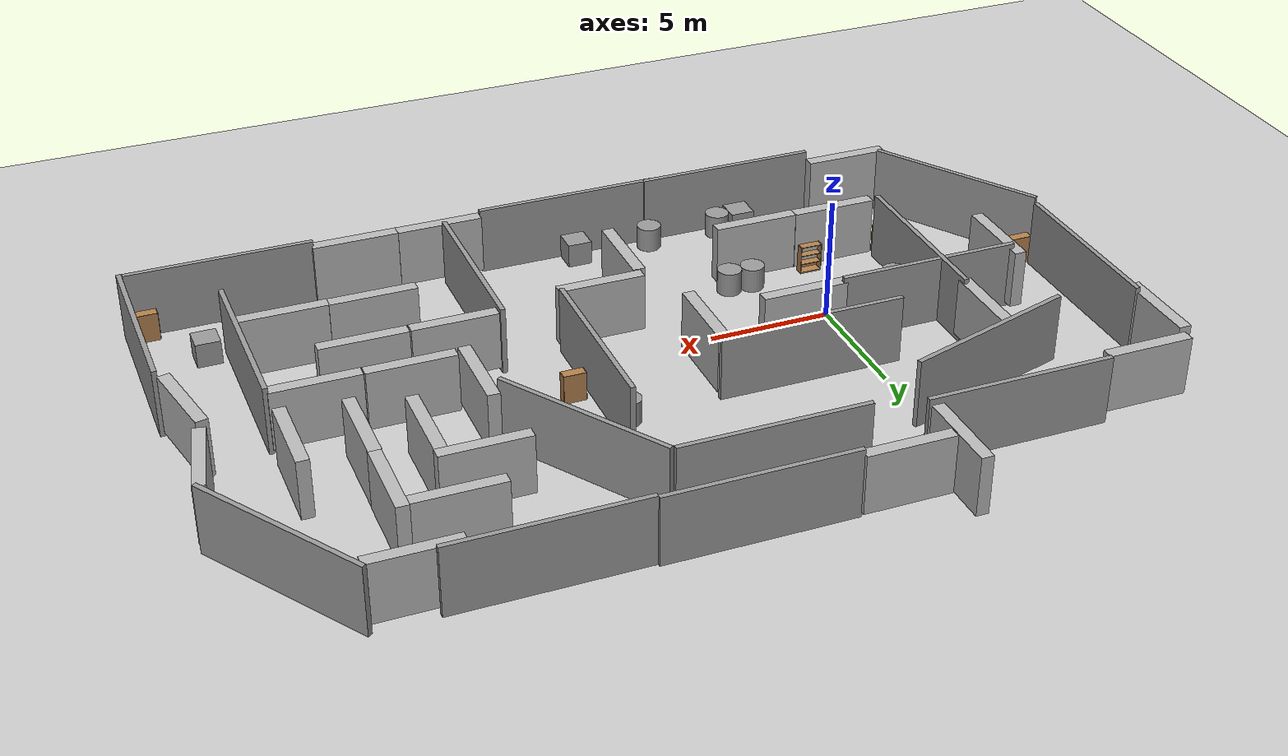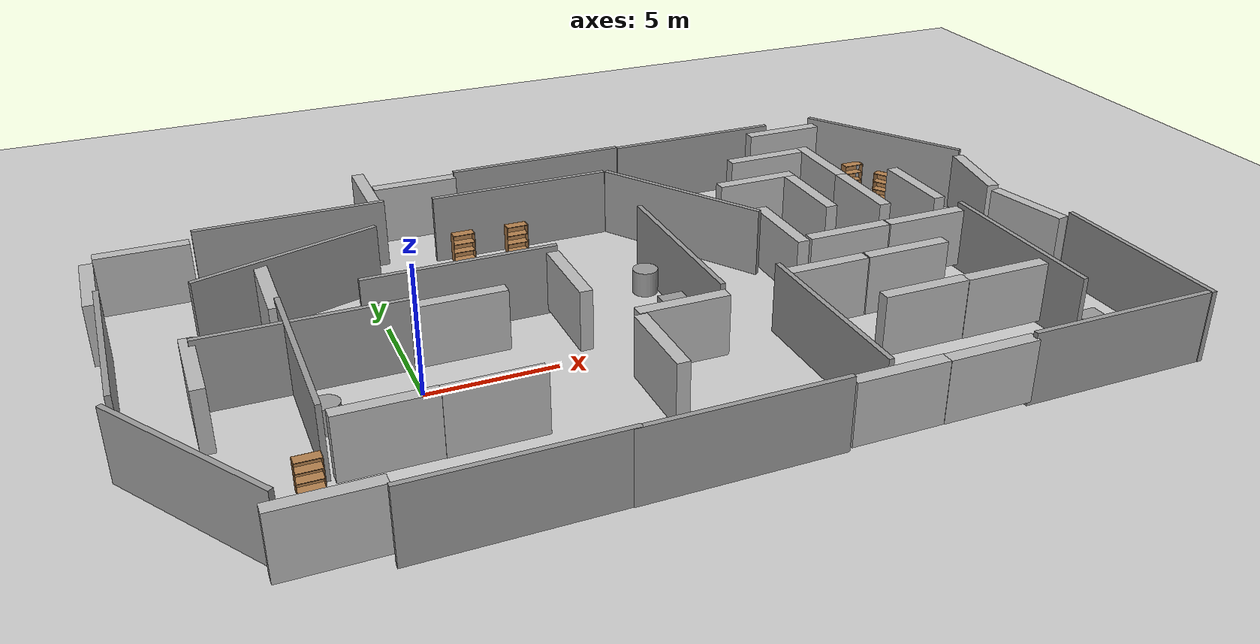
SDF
<sdf version="1.6">
 <world name="default">
  <light name="sun" type="directional">
   <pose>0 0 10 0 -0 0</pose>
   <diffuse>0.8 0.8 0.8 1</diffuse>
   <specular>0.1 0.1 0.1 1</specular>
   <attenuation>
    <range>1000</range>
    <constant>0.9</constant>
    <linear>0.01</linear>
    <quadratic>0.001</quadratic>
   </attenuation>
   <direction>-0.5 0.5 -1</direction>
  </light>
  <model name="ground_plane">
   <static>1</static>
   <link name="link">
    <collision name="collision">
     <geometry><plane><normal>0 0 1</normal><size>100 100</size></plane></geometry>
     <surface><friction><ode><mu>100</mu><mu2>50</mu2></ode></friction></surface>
    </collision>
    <visual name="visual">
     <cast_shadows>0</cast_shadows>
     <geometry><plane><normal>0 0 1</normal><size>100 100</size></plane></geometry>
     <material>
      <script><uri>file://media/materials/scripts/gazebo.material</uri><name>Gazebo/Grey</name></script>
     </material>
    </visual>
   </link>
  </model>
  <gravity>0 0 -9.8</gravity>
  <magnetic_field>6e-06 2.3e-05 -4.2e-05</magnetic_field>
  <atmosphere type="adiabatic"/>
  <physics name="default_physics" default="0" type="ode">
   <max_step_size>0.001</max_step_size>
   <real_time_factor>1</real_time_factor>
   <real_time_update_rate>1000</real_time_update_rate>
  </physics>
  <scene><ambient>0.4 0.4 0.4 1</ambient><background>0.7 0.7 0.7 1</background><shadows>1</shadows></scene>
  <spherical_coordinates>
   <surface_model>EARTH_WGS84</surface_model>
   <latitude_deg>0</latitude_deg>
   <longitude_deg>0</longitude_deg>
   <elevation>0</elevation>
   <heading_deg>0</heading_deg>
  </spherical_coordinates>
  <model name="grey_wall">
   <static>1</static>
   <link name="link">
    <pose>0 0 1.4 0 -0 0</pose>
    <collision name="collision"><geometry><box><size>7.5 0.2 2.8</size></box></geometry></collision>
    <visual name="visual">
     <cast_shadows>0</cast_shadows>
     <geometry><box><size>7.5 0.2 2.8</size></box></geometry>
     <material>
      <script>
       <uri>model://grey_wall/materials/scripts</uri>
       <uri>model://grey_wall/materials/textures</uri>
       <name>vrc/grey_wall</name>
      </script>
     </material>
    </visual>
   </link>
   <pose>-2.38225 10.6143 0 0 -0 0</pose>
  </model>
  <model name="unit_box_0">
   <pose>-2.56657 10.0143 0.5 0 0 -1e-05</pose>
   <link name="link">
    <inertial>
     <mass>1</mass>
     <inertia>
      <ixx>0.166667</ixx>
      <ixy>0</ixy>
      <ixz>0</ixz>
      <iyy>0.166667</iyy>
      <iyz>0</iyz>
      <izz>0.166667</izz>
     </inertia>
    </inertial>
    <collision name="collision"><geometry><box><size>1 1 1</size></box></geometry></collision>
    <visual name="visual">
     <geometry><box><size>1 1 1</size></box></geometry>
     <material>
      <script><name>Gazebo/Grey</name><uri>file://media/materials/scripts/gazebo.material</uri></script>
     </material>
    </visual>
   </link>
  </model>
  <model name="grey_wall_0">
   <static>1</static>
   <link name="link">
    <pose>0 0 1.4 0 -0 0</pose>
    <collision name="collision"><geometry><box><size>7.5 0.2 2.8</size></box></geometry></collision>
    <visual name="visual">
     <cast_shadows>0</cast_shadows>
     <geometry><box><size>7.5 0.2 2.8</size></box></geometry>
     <material>
      <script>
       <uri>model://grey_wall/materials/scripts</uri>
       <uri>model://grey_wall/materials/textures</uri>
       <name>vrc/grey_wall</name>
      </script>
     </material>
    </visual>
   </link>
   <pose>7 10.0868 0 0 -0 0</pose>
  </model>
  <model name="bookshelf_0">
   <static>1</static>
   <link name="link">
    <inertial><mass>1</mass></inertial>
    <collision name="back">
     <pose>0 0.005 0.6 0 -0 0</pose>
     <geometry><box><size>0.9 0.01 1.2</size></box></geometry>
    </collision>
    <visual name="visual1">
     <pose>0 0.005 0.6 0 -0 0</pose>
     <geometry><box><size>0.9 0.01 1.2</size></box></geometry>
     <material>
      <script><uri>file://media/materials/scripts/gazebo.material</uri><name>Gazebo/Wood</name></script>
     </material>
    </visual>
    <collision name="left_side">
     <pose>0.45 -0.195 0.6 0 -0 0</pose>
     <geometry><box><size>0.02 0.4 1.2</size></box></geometry>
    </collision>
    <visual name="visual2">
     <pose>0.45 -0.195 0.6 0 -0 0</pose>
     <geometry><box><size>0.02 0.4 1.2</size></box></geometry>
     <material>
      <script><uri>file://media/materials/scripts/gazebo.material</uri><name>Gazebo/Wood</name></script>
     </material>
    </visual>
    <collision name="right_side">
     <pose>-0.45 -0.195 0.6 0 -0 0</pose>
     <geometry><box><size>0.02 0.4 1.2</size></box></geometry>
    </collision>
    <visual name="visual3">
     <pose>-0.45 -0.195 0.6 0 -0 0</pose>
     <geometry><box><size>0.02 0.4 1.2</size></box></geometry>
     <material>
      <script><uri>file://media/materials/scripts/gazebo.material</uri><name>Gazebo/Wood</name></script>
     </material>
    </visual>
    <collision name="bottom">
     <pose>0 -0.195 0.03 0 -0 0</pose>
     <geometry><box><size>0.88 0.4 0.06</size></box></geometry>
    </collision>
    <visual name="visual4">
     <pose>0 -0.195 0.03 0 -0 0</pose>
     <geometry><box><size>0.88 0.4 0.06</size></box></geometry>
     <material>
      <script><uri>file://media/materials/scripts/gazebo.material</uri><name>Gazebo/Wood</name></script>
     </material>
    </visual>
    <collision name="top">
     <pose>0 -0.195 1.19 0 -0 0</pose>
     <geometry><box><size>0.88 0.4 0.02</size></box></geometry>
    </collision>
    <visual name="visual5">
     <pose>0 -0.195 1.19 0 -0 0</pose>
     <geometry><box><size>0.88 0.4 0.02</size></box></geometry>
     <material>
      <script><uri>file://media/materials/scripts/gazebo.material</uri><name>Gazebo/Wood</name></script>
     </material>
    </visual>
    <collision name="low_shelf">
     <pose>0 -0.195 0.43 0 -0 0</pose>
     <geometry><box><size>0.88 0.4 0.02</size></box></geometry>
    </collision>
    <visual name="visual6">
     <pose>0 -0.195 0.43 0 -0 0</pose>
     <geometry><box><size>0.88 0.4 0.02</size></box></geometry>
     <material>
      <script><uri>file://media/materials/scripts/gazebo.material</uri><name>Gazebo/Wood</name></script>
     </material>
    </visual>
    <collision name="high_shelf">
     <pose>0 -0.195 0.8 0 -0 0</pose>
     <geometry><box><size>0.88 0.4 0.02</size></box></geometry>
    </collision>
    <visual name="visual7">
     <pose>0 -0.195 0.8 0 -0 0</pose>
     <geometry><box><size>0.88 0.4 0.02</size></box></geometry>
     <material>
      <script><uri>file://media/materials/scripts/gazebo.material</uri><name>Gazebo/Wood</name></script>
     </material>
    </visual>
   </link>
   <pose>4.33067 9.93272 0 0 -0 0</pose>
  </model>
  <model name="bookshelf_1">
   <static>1</static>
   <link name="link">
    <inertial><mass>1</mass></inertial>
    <collision name="back">
     <pose>0 0.005 0.6 0 -0 0</pose>
     <geometry><box><size>0.9 0.01 1.2</size></box></geometry>
    </collision>
    <visual name="visual1">
     <pose>0 0.005 0.6 0 -0 0</pose>
     <geometry><box><size>0.9 0.01 1.2</size></box></geometry>
     <material>
      <script><uri>file://media/materials/scripts/gazebo.material</uri><name>Gazebo/Wood</name></script>
     </material>
    </visual>
    <collision name="left_side">
     <pose>0.45 -0.195 0.6 0 -0 0</pose>
     <geometry><box><size>0.02 0.4 1.2</size></box></geometry>
    </collision>
    <visual name="visual2">
     <pose>0.45 -0.195 0.6 0 -0 0</pose>
     <geometry><box><size>0.02 0.4 1.2</size></box></geometry>
     <material>
      <script><uri>file://media/materials/scripts/gazebo.material</uri><name>Gazebo/Wood</name></script>
     </material>
    </visual>
    <collision name="right_side">
     <pose>-0.45 -0.195 0.6 0 -0 0</pose>
     <geometry><box><size>0.02 0.4 1.2</size></box></geometry>
    </collision>
    <visual name="visual3">
     <pose>-0.45 -0.195 0.6 0 -0 0</pose>
     <geometry><box><size>0.02 0.4 1.2</size></box></geometry>
     <material>
      <script><uri>file://media/materials/scripts/gazebo.material</uri><name>Gazebo/Wood</name></script>
     </material>
    </visual>
    <collision name="bottom">
     <pose>0 -0.195 0.03 0 -0 0</pose>
     <geometry><box><size>0.88 0.4 0.06</size></box></geometry>
    </collision>
    <visual name="visual4">
     <pose>0 -0.195 0.03 0 -0 0</pose>
     <geometry><box><size>0.88 0.4 0.06</size></box></geometry>
     <material>
      <script><uri>file://media/materials/scripts/gazebo.material</uri><name>Gazebo/Wood</name></script>
     </material>
    </visual>
    <collision name="top">
     <pose>0 -0.195 1.19 0 -0 0</pose>
     <geometry><box><size>0.88 0.4 0.02</size></box></geometry>
    </collision>
    <visual name="visual5">
     <pose>0 -0.195 1.19 0 -0 0</pose>
     <geometry><box><size>0.88 0.4 0.02</size></box></geometry>
     <material>
      <script><uri>file://media/materials/scripts/gazebo.material</uri><name>Gazebo/Wood</name></script>
     </material>
    </visual>
    <collision name="low_shelf">
     <pose>0 -0.195 0.43 0 -0 0</pose>
     <geometry><box><size>0.88 0.4 0.02</size></box></geometry>
    </collision>
    <visual name="visual6">
     <pose>0 -0.195 0.43 0 -0 0</pose>
     <geometry><box><size>0.88 0.4 0.02</size></box></geometry>
     <material>
      <script><uri>file://media/materials/scripts/gazebo.material</uri><name>Gazebo/Wood</name></script>
     </material>
    </visual>
    <collision name="high_shelf">
     <pose>0 -0.195 0.8 0 -0 0</pose>
     <geometry><box><size>0.88 0.4 0.02</size></box></geometry>
    </collision>
    <visual name="visual7">
     <pose>0 -0.195 0.8 0 -0 0</pose>
     <geometry><box><size>0.88 0.4 0.02</size></box></geometry>
     <material>
      <script><uri>file://media/materials/scripts/gazebo.material</uri><name>Gazebo/Wood</name></script>
     </material>
    </visual>
   </link>
   <pose>6.61961 9.86481 0 0 -0 0</pose>
  </model>
  <model name="grey_wall_1">
   <static>1</static>
   <link name="link">
    <pose>0 0 1.4 0 -0 0</pose>
    <collision name="collision"><geometry><box><size>7.5 0.2 2.8</size></box></geometry></collision>
    <visual name="visual">
     <cast_shadows>0</cast_shadows>
     <geometry><box><size>7.5 0.2 2.8</size></box></geometry>
     <material>
      <script>
       <uri>model://grey_wall/materials/scripts</uri>
       <uri>model://grey_wall/materials/textures</uri>
       <name>vrc/grey_wall</name>
      </script>
     </material>
    </visual>
   </link>
   <pose>-9.75377 3 0 0 -0 1.57</pose>
  </model>
  <model name="grey_wall_2">
   <static>1</static>
   <link name="link">
    <pose>0 0 1.4 0 -0 0</pose>
    <collision name="collision"><geometry><box><size>7.5 0.2 2.8</size></box></geometry></collision>
    <visual name="visual">
     <cast_shadows>0</cast_shadows>
     <geometry><box><size>7.5 0.2 2.8</size></box></geometry>
     <material>
      <script>
       <uri>model://grey_wall/materials/scripts</uri>
       <uri>model://grey_wall/materials/textures</uri>
       <name>vrc/grey_wall</name>
      </script>
     </material>
    </visual>
   </link>
   <pose>10.7049 2.36121 0 0 -0 1.57</pose>
  </model>
  <model name="unit_cylinder_0_0">
   <pose>10.1063 4.12187 0.5 0 -0 1.1e-05</pose>
   <link name="link">
    <inertial>
     <mass>1</mass>
     <inertia><ixx>0.145833</ixx><ixy>0</ixy><ixz>0</ixz><iyy>0.145833</iyy><iyz>0</iyz><izz>0.125</izz></inertia>
    </inertial>
    <collision name="collision">
     <geometry><cylinder><radius>0.5</radius><length>1</length></cylinder></geometry>
    </collision>
    <visual name="visual">
     <geometry><cylinder><radius>0.5</radius><length>1</length></cylinder></geometry>
     <material>
      <script><name>Gazebo/Grey</name><uri>file://media/materials/scripts/gazebo.material</uri></script>
     </material>
    </visual>
   </link>
  </model>
  <model name="unit_box_1_0">
   <pose>10.1038 1.31079 0.499995 0 1e-05 -0.000339</pose>
   <link name="link">
    <inertial>
     <mass>1</mass>
     <inertia>
      <ixx>0.166667</ixx>
      <ixy>0</ixy>
      <ixz>0</ixz>
      <iyy>0.166667</iyy>
      <iyz>0</iyz>
      <izz>0.166667</izz>
     </inertia>
    </inertial>
    <collision name="collision"><geometry><box><size>1 1 1</size></box></geometry></collision>
    <visual name="visual">
     <geometry><box><size>1 1 1</size></box></geometry>
     <material>
      <script><name>Gazebo/Grey</name><uri>file://media/materials/scripts/gazebo.material</uri></script>
     </material>
    </visual>
   </link>
  </model>
  <model name="grey_wall_3">
   <static>1</static>
   <link name="link">
    <pose>0 0 1.4 0 -0 0</pose>
    <collision name="collision"><geometry><box><size>7.5 0.2 2.8</size></box></geometry></collision>
    <visual name="visual">
     <cast_shadows>0</cast_shadows>
     <geometry><box><size>7.5 0.2 2.8</size></box></geometry>
     <material>
      <script>
       <uri>model://grey_wall/materials/scripts</uri>
       <uri>model://grey_wall/materials/textures</uri>
       <name>vrc/grey_wall</name>
      </script>
     </material>
    </visual>
   </link>
   <pose>-8 -4.35516 0 0 0 -1</pose>
  </model>
  <model name="bookshelf_2">
   <static>1</static>
   <link name="link">
    <inertial><mass>1</mass></inertial>
    <collision name="back">
     <pose>0 0.005 0.6 0 -0 0</pose>
     <geometry><box><size>0.9 0.01 1.2</size></box></geometry>
    </collision>
    <visual name="visual1">
     <pose>0 0.005 0.6 0 -0 0</pose>
     <geometry><box><size>0.9 0.01 1.2</size></box></geometry>
     <material>
      <script><uri>file://media/materials/scripts/gazebo.material</uri><name>Gazebo/Wood</name></script>
     </material>
    </visual>
    <collision name="left_side">
     <pose>0.45 -0.195 0.6 0 -0 0</pose>
     <geometry><box><size>0.02 0.4 1.2</size></box></geometry>
    </collision>
    <visual name="visual2">
     <pose>0.45 -0.195 0.6 0 -0 0</pose>
     <geometry><box><size>0.02 0.4 1.2</size></box></geometry>
     <material>
      <script><uri>file://media/materials/scripts/gazebo.material</uri><name>Gazebo/Wood</name></script>
     </material>
    </visual>
    <collision name="right_side">
     <pose>-0.45 -0.195 0.6 0 -0 0</pose>
     <geometry><box><size>0.02 0.4 1.2</size></box></geometry>
    </collision>
    <visual name="visual3">
     <pose>-0.45 -0.195 0.6 0 -0 0</pose>
     <geometry><box><size>0.02 0.4 1.2</size></box></geometry>
     <material>
      <script><uri>file://media/materials/scripts/gazebo.material</uri><name>Gazebo/Wood</name></script>
     </material>
    </visual>
    <collision name="bottom">
     <pose>0 -0.195 0.03 0 -0 0</pose>
     <geometry><box><size>0.88 0.4 0.06</size></box></geometry>
    </collision>
    <visual name="visual4">
     <pose>0 -0.195 0.03 0 -0 0</pose>
     <geometry><box><size>0.88 0.4 0.06</size></box></geometry>
     <material>
      <script><uri>file://media/materials/scripts/gazebo.material</uri><name>Gazebo/Wood</name></script>
     </material>
    </visual>
    <collision name="top">
     <pose>0 -0.195 1.19 0 -0 0</pose>
     <geometry><box><size>0.88 0.4 0.02</size></box></geometry>
    </collision>
    <visual name="visual5">
     <pose>0 -0.195 1.19 0 -0 0</pose>
     <geometry><box><size>0.88 0.4 0.02</size></box></geometry>
     <material>
      <script><uri>file://media/materials/scripts/gazebo.material</uri><name>Gazebo/Wood</name></script>
     </material>
    </visual>
    <collision name="low_shelf">
     <pose>0 -0.195 0.43 0 -0 0</pose>
     <geometry><box><size>0.88 0.4 0.02</size></box></geometry>
    </collision>
    <visual name="visual6">
     <pose>0 -0.195 0.43 0 -0 0</pose>
     <geometry><box><size>0.88 0.4 0.02</size></box></geometry>
     <material>
      <script><uri>file://media/materials/scripts/gazebo.material</uri><name>Gazebo/Wood</name></script>
     </material>
    </visual>
    <collision name="high_shelf">
     <pose>0 -0.195 0.8 0 -0 0</pose>
     <geometry><box><size>0.88 0.4 0.02</size></box></geometry>
    </collision>
    <visual name="visual7">
     <pose>0 -0.195 0.8 0 -0 0</pose>
     <geometry><box><size>0.88 0.4 0.02</size></box></geometry>
     <material>
      <script><uri>file://media/materials/scripts/gazebo.material</uri><name>Gazebo/Wood</name></script>
     </material>
    </visual>
   </link>
   <pose>-9.31763 -0.823103 0 0 -0 0</pose>
  </model>
  <model name="grey_wall_4">
   <static>1</static>
   <link name="link">
    <pose>0 0 1.4 0 -0 0</pose>
    <collision name="collision"><geometry><box><size>7.5 0.2 2.8</size></box></geometry></collision>
    <visual name="visual">
     <cast_shadows>0</cast_shadows>
     <geometry><box><size>7.5 0.2 2.8</size></box></geometry>
     <material>
      <script>
       <uri>model://grey_wall/materials/scripts</uri>
       <uri>model://grey_wall/materials/textures</uri>
       <name>vrc/grey_wall</name>
      </script>
     </material>
    </visual>
   </link>
   <pose>0.732873 -8.54775 0 0 -0 0</pose>
  </model>
  <model name="grey_wall_5">
   <static>1</static>
   <link name="link">
    <pose>0 0 1.4 0 -0 0</pose>
    <collision name="collision"><geometry><box><size>7.5 0.2 2.8</size></box></geometry></collision>
    <visual name="visual">
     <cast_shadows>0</cast_shadows>
     <geometry><box><size>7.5 0.2 2.8</size></box></geometry>
     <material>
      <script>
       <uri>model://grey_wall/materials/scripts</uri>
       <uri>model://grey_wall/materials/textures</uri>
       <name>vrc/grey_wall</name>
      </script>
     </material>
    </visual>
   </link>
   <pose>7.91479 -8.57466 0 0 -0 0</pose>
  </model>
  <model name="unit_box_1_1">
   <pose>0.35925 -7.94761 0.499995 0 1e-05 0.000272</pose>
   <link name="link">
    <inertial>
     <mass>1</mass>
     <inertia>
      <ixx>0.166667</ixx>
      <ixy>0</ixy>
      <ixz>0</ixz>
      <iyy>0.166667</iyy>
      <iyz>0</iyz>
      <izz>0.166667</izz>
     </inertia>
    </inertial>
    <collision name="collision"><geometry><box><size>1 1 1</size></box></geometry></collision>
    <visual name="visual">
     <geometry><box><size>1 1 1</size></box></geometry>
     <material>
      <script><name>Gazebo/Grey</name><uri>file://media/materials/scripts/gazebo.material</uri></script>
     </material>
    </visual>
   </link>
  </model>
  <model name="unit_cylinder_0_1">
   <pose>1.35926 -7.91818 0.499994 -3e-06 -1e-06 -0.00033</pose>
   <link name="link">
    <inertial>
     <mass>1</mass>
     <inertia><ixx>0.145833</ixx><ixy>0</ixy><ixz>0</ixz><iyy>0.145833</iyy><iyz>0</iyz><izz>0.125</izz></inertia>
    </inertial>
    <collision name="collision">
     <geometry><cylinder><radius>0.5</radius><length>1</length></cylinder></geometry>
    </collision>
    <visual name="visual">
     <geometry><cylinder><radius>0.5</radius><length>1</length></cylinder></geometry>
     <material>
      <script><name>Gazebo/Grey</name><uri>file://media/materials/scripts/gazebo.material</uri></script>
     </material>
    </visual>
   </link>
  </model>
  <model name="unit_cylinder_0_2">
   <pose>4.46936 -7.94617 0.499994 -3e-06 -1e-06 -0</pose>
   <link name="link">
    <inertial>
     <mass>1</mass>
     <inertia><ixx>0.145833</ixx><ixy>0</ixy><ixz>0</ixz><iyy>0.145833</iyy><iyz>0</iyz><izz>0.125</izz></inertia>
    </inertial>
    <collision name="collision">
     <geometry><cylinder><radius>0.5</radius><length>1</length></cylinder></geometry>
    </collision>
    <visual name="visual">
     <geometry><cylinder><radius>0.5</radius><length>1</length></cylinder></geometry>
     <material>
      <script><name>Gazebo/Grey</name><uri>file://media/materials/scripts/gazebo.material</uri></script>
     </material>
    </visual>
   </link>
  </model>
  <model name="unit_box_1_2">
   <pose>7.72225 -7.97465 0.499995 0 -1e-05 7e-06</pose>
   <link name="link">
    <inertial>
     <mass>1</mass>
     <inertia>
      <ixx>0.166667</ixx>
      <ixy>0</ixy>
      <ixz>0</ixz>
      <iyy>0.166667</iyy>
      <iyz>0</iyz>
      <izz>0.166667</izz>
     </inertia>
    </inertial>
    <collision name="collision"><geometry><box><size>1 1 1</size></box></geometry></collision>
    <visual name="visual">
     <geometry><box><size>1 1 1</size></box></geometry>
     <material>
      <script><name>Gazebo/Grey</name><uri>file://media/materials/scripts/gazebo.material</uri></script>
     </material>
    </visual>
   </link>
  </model>
  <model name="grey_wall_6">
   <static>1</static>
   <link name="link">
    <pose>0 0 1.4 0 -0 0</pose>
    <collision name="collision"><geometry><box><size>7.5 0.2 2.8</size></box></geometry></collision>
    <visual name="visual">
     <cast_shadows>0</cast_shadows>
     <geometry><box><size>7.5 0.2 2.8</size></box></geometry>
     <material>
      <script>
       <uri>model://grey_wall/materials/scripts</uri>
       <uri>model://grey_wall/materials/textures</uri>
       <name>vrc/grey_wall</name>
      </script>
     </material>
    </visual>
   </link>
   <pose>-3.07893 7.22093 0 0 -0 0.3</pose>
  </model>
  <model name="grey_wall_7">
   <static>1</static>
   <link name="link">
    <pose>0 0 1.4 0 -0 0</pose>
    <collision name="collision"><geometry><box><size>7.5 0.2 2.8</size></box></geometry></collision>
    <visual name="visual">
     <cast_shadows>0</cast_shadows>
     <geometry><box><size>7.5 0.2 2.8</size></box></geometry>
     <material>
      <script>
       <uri>model://grey_wall/materials/scripts</uri>
       <uri>model://grey_wall/materials/textures</uri>
       <name>vrc/grey_wall</name>
      </script>
     </material>
    </visual>
   </link>
   <pose>-4 0 0 0 -0 1.57</pose>
  </model>
  <model name="grey_wall_8">
   <static>1</static>
   <link name="link">
    <pose>0 0 1.4 0 -0 0</pose>
    <collision name="collision"><geometry><box><size>7.5 0.2 2.8</size></box></geometry></collision>
    <visual name="visual">
     <cast_shadows>0</cast_shadows>
     <geometry><box><size>7.5 0.2 2.8</size></box></geometry>
     <material>
      <script>
       <uri>model://grey_wall/materials/scripts</uri>
       <uri>model://grey_wall/materials/textures</uri>
       <name>vrc/grey_wall</name>
      </script>
     </material>
    </visual>
   </link>
   <pose>-3.41531 1.85779 0 0 -0 0</pose>
  </model>
  <model name="bookshelf_3">
   <static>1</static>
   <link name="link">
    <inertial><mass>1</mass></inertial>
    <collision name="back">
     <pose>0 0.005 0.6 0 -0 0</pose>
     <geometry><box><size>0.9 0.01 1.2</size></box></geometry>
    </collision>
    <visual name="visual1">
     <pose>0 0.005 0.6 0 -0 0</pose>
     <geometry><box><size>0.9 0.01 1.2</size></box></geometry>
     <material>
      <script><uri>file://media/materials/scripts/gazebo.material</uri><name>Gazebo/Wood</name></script>
     </material>
    </visual>
    <collision name="left_side">
     <pose>0.45 -0.195 0.6 0 -0 0</pose>
     <geometry><box><size>0.02 0.4 1.2</size></box></geometry>
    </collision>
    <visual name="visual2">
     <pose>0.45 -0.195 0.6 0 -0 0</pose>
     <geometry><box><size>0.02 0.4 1.2</size></box></geometry>
     <material>
      <script><uri>file://media/materials/scripts/gazebo.material</uri><name>Gazebo/Wood</name></script>
     </material>
    </visual>
    <collision name="right_side">
     <pose>-0.45 -0.195 0.6 0 -0 0</pose>
     <geometry><box><size>0.02 0.4 1.2</size></box></geometry>
    </collision>
    <visual name="visual3">
     <pose>-0.45 -0.195 0.6 0 -0 0</pose>
     <geometry><box><size>0.02 0.4 1.2</size></box></geometry>
     <material>
      <script><uri>file://media/materials/scripts/gazebo.material</uri><name>Gazebo/Wood</name></script>
     </material>
    </visual>
    <collision name="bottom">
     <pose>0 -0.195 0.03 0 -0 0</pose>
     <geometry><box><size>0.88 0.4 0.06</size></box></geometry>
    </collision>
    <visual name="visual4">
     <pose>0 -0.195 0.03 0 -0 0</pose>
     <geometry><box><size>0.88 0.4 0.06</size></box></geometry>
     <material>
      <script><uri>file://media/materials/scripts/gazebo.material</uri><name>Gazebo/Wood</name></script>
     </material>
    </visual>
    <collision name="top">
     <pose>0 -0.195 1.19 0 -0 0</pose>
     <geometry><box><size>0.88 0.4 0.02</size></box></geometry>
    </collision>
    <visual name="visual5">
     <pose>0 -0.195 1.19 0 -0 0</pose>
     <geometry><box><size>0.88 0.4 0.02</size></box></geometry>
     <material>
      <script><uri>file://media/materials/scripts/gazebo.material</uri><name>Gazebo/Wood</name></script>
     </material>
    </visual>
    <collision name="low_shelf">
     <pose>0 -0.195 0.43 0 -0 0</pose>
     <geometry><box><size>0.88 0.4 0.02</size></box></geometry>
    </collision>
    <visual name="visual6">
     <pose>0 -0.195 0.43 0 -0 0</pose>
     <geometry><box><size>0.88 0.4 0.02</size></box></geometry>
     <material>
      <script><uri>file://media/materials/scripts/gazebo.material</uri><name>Gazebo/Wood</name></script>
     </material>
    </visual>
    <collision name="high_shelf">
     <pose>0 -0.195 0.8 0 -0 0</pose>
     <geometry><box><size>0.88 0.4 0.02</size></box></geometry>
    </collision>
    <visual name="visual7">
     <pose>0 -0.195 0.8 0 -0 0</pose>
     <geometry><box><size>0.88 0.4 0.02</size></box></geometry>
     <material>
      <script><uri>file://media/materials/scripts/gazebo.material</uri><name>Gazebo/Wood</name></script>
     </material>
    </visual>
   </link>
   <pose>-4.55124 -3.7724 0 0 -0 0</pose>
  </model>
  <model name="unit_cylinder_0_3">
   <pose>-3.38655 -0.778176 0.499996 3e-06 1e-06 -0</pose>
   <link name="link">
    <inertial>
     <mass>1</mass>
     <inertia><ixx>0.145833</ixx><ixy>0</ixy><ixz>0</ixz><iyy>0.145833</iyy><iyz>0</iyz><izz>0.125</izz></inertia>
    </inertial>
    <collision name="collision">
     <geometry><cylinder><radius>0.5</radius><length>1</length></cylinder></geometry>
    </collision>
    <visual name="visual">
     <geometry><cylinder><radius>0.5</radius><length>1</length></cylinder></geometry>
     <material>
      <script><name>Gazebo/Grey</name><uri>file://media/materials/scripts/gazebo.material</uri></script>
     </material>
    </visual>
   </link>
  </model>
  <model name="bookshelf_4">
   <static>1</static>
   <link name="link">
    <inertial><mass>1</mass></inertial>
    <collision name="back">
     <pose>0 0.005 0.6 0 -0 0</pose>
     <geometry><box><size>0.9 0.01 1.2</size></box></geometry>
    </collision>
    <visual name="visual1">
     <pose>0 0.005 0.6 0 -0 0</pose>
     <geometry><box><size>0.9 0.01 1.2</size></box></geometry>
     <material>
      <script><uri>file://media/materials/scripts/gazebo.material</uri><name>Gazebo/Wood</name></script>
     </material>
    </visual>
    <collision name="left_side">
     <pose>0.45 -0.195 0.6 0 -0 0</pose>
     <geometry><box><size>0.02 0.4 1.2</size></box></geometry>
    </collision>
    <visual name="visual2">
     <pose>0.45 -0.195 0.6 0 -0 0</pose>
     <geometry><box><size>0.02 0.4 1.2</size></box></geometry>
     <material>
      <script><uri>file://media/materials/scripts/gazebo.material</uri><name>Gazebo/Wood</name></script>
     </material>
    </visual>
    <collision name="right_side">
     <pose>-0.45 -0.195 0.6 0 -0 0</pose>
     <geometry><box><size>0.02 0.4 1.2</size></box></geometry>
    </collision>
    <visual name="visual3">
     <pose>-0.45 -0.195 0.6 0 -0 0</pose>
     <geometry><box><size>0.02 0.4 1.2</size></box></geometry>
     <material>
      <script><uri>file://media/materials/scripts/gazebo.material</uri><name>Gazebo/Wood</name></script>
     </material>
    </visual>
    <collision name="bottom">
     <pose>0 -0.195 0.03 0 -0 0</pose>
     <geometry><box><size>0.88 0.4 0.06</size></box></geometry>
    </collision>
    <visual name="visual4">
     <pose>0 -0.195 0.03 0 -0 0</pose>
     <geometry><box><size>0.88 0.4 0.06</size></box></geometry>
     <material>
      <script><uri>file://media/materials/scripts/gazebo.material</uri><name>Gazebo/Wood</name></script>
     </material>
    </visual>
    <collision name="top">
     <pose>0 -0.195 1.19 0 -0 0</pose>
     <geometry><box><size>0.88 0.4 0.02</size></box></geometry>
    </collision>
    <visual name="visual5">
     <pose>0 -0.195 1.19 0 -0 0</pose>
     <geometry><box><size>0.88 0.4 0.02</size></box></geometry>
     <material>
      <script><uri>file://media/materials/scripts/gazebo.material</uri><name>Gazebo/Wood</name></script>
     </material>
    </visual>
    <collision name="low_shelf">
     <pose>0 -0.195 0.43 0 -0 0</pose>
     <geometry><box><size>0.88 0.4 0.02</size></box></geometry>
    </collision>
    <visual name="visual6">
     <pose>0 -0.195 0.43 0 -0 0</pose>
     <geometry><box><size>0.88 0.4 0.02</size></box></geometry>
     <material>
      <script><uri>file://media/materials/scripts/gazebo.material</uri><name>Gazebo/Wood</name></script>
     </material>
    </visual>
    <collision name="high_shelf">
     <pose>0 -0.195 0.8 0 -0 0</pose>
     <geometry><box><size>0.88 0.4 0.02</size></box></geometry>
    </collision>
    <visual name="visual7">
     <pose>0 -0.195 0.8 0 -0 0</pose>
     <geometry><box><size>0.88 0.4 0.02</size></box></geometry>
     <material>
      <script><uri>file://media/materials/scripts/gazebo.material</uri><name>Gazebo/Wood</name></script>
     </material>
    </visual>
   </link>
   <pose>-0.924476 -3.8 0 0 -0 3.14</pose>
  </model>
  <model name="unit_cylinder_0_4">
   <pose>1.82135 -3.23102 0.50045 -0.000753 -0.000505 -0.030917</pose>
   <link name="link">
    <inertial>
     <mass>1</mass>
     <inertia><ixx>0.145833</ixx><ixy>0</ixy><ixz>0</ixz><iyy>0.145833</iyy><iyz>0</iyz><izz>0.125</izz></inertia>
    </inertial>
    <collision name="collision">
     <geometry><cylinder><radius>0.5</radius><length>1</length></cylinder></geometry>
    </collision>
    <visual name="visual">
     <geometry><cylinder><radius>0.5</radius><length>1</length></cylinder></geometry>
     <material>
      <script><name>Gazebo/Grey</name><uri>file://media/materials/scripts/gazebo.material</uri></script>
     </material>
    </visual>
   </link>
  </model>
  <model name="unit_cylinder_0_5">
   <pose>2.8235 -3.25312 0.499993 -3e-06 -1e-06 -0.035597</pose>
   <link name="link">
    <inertial>
     <mass>1</mass>
     <inertia><ixx>0.145833</ixx><ixy>0</ixy><ixz>0</ixz><iyy>0.145833</iyy><iyz>0</iyz><izz>0.125</izz></inertia>
    </inertial>
    <collision name="collision">
     <geometry><cylinder><radius>0.5</radius><length>1</length></cylinder></geometry>
    </collision>
    <visual name="visual">
     <geometry><cylinder><radius>0.5</radius><length>1</length></cylinder></geometry>
     <material>
      <script><name>Gazebo/Grey</name><uri>file://media/materials/scripts/gazebo.material</uri></script>
     </material>
    </visual>
   </link>
  </model>
  <model name="grey_wall_9">
   <static>1</static>
   <link name="link">
    <pose>0 0 1.4 0 -0 0</pose>
    <collision name="collision"><geometry><box><size>7.5 0.2 2.8</size></box></geometry></collision>
    <visual name="visual">
     <cast_shadows>0</cast_shadows>
     <geometry><box><size>7.5 0.2 2.8</size></box></geometry>
     <material>
      <script>
       <uri>model://grey_wall/materials/scripts</uri>
       <uri>model://grey_wall/materials/textures</uri>
       <name>vrc/grey_wall</name>
      </script>
     </material>
    </visual>
   </link>
   <pose>2.64896 3.98891 0 0 -0 0</pose>
  </model>
  <model name="mywall1">
   <static>1</static>
   <link name="link">
    <pose>0 0 1.4 0 -0 0</pose>
    <collision name="collision"><geometry><box><size>3.5 0.5 2.4</size></box></geometry></collision>
    <visual name="visual">
     <cast_shadows>0</cast_shadows>
     <geometry><box><size>3.5 0.5 2.4</size></box></geometry>
     <material>
      <script>
       <uri>model://mywall1/materials/scripts</uri>
       <uri>model://mywall1/materials/textures</uri>
       <name>vrc/mywall1</name>
      </script>
     </material>
    </visual>
   </link>
   <pose>-10 7.81498 0 0 -0 1.57</pose>
  </model>
  <model name="mywall1_0">
   <static>1</static>
   <link name="link">
    <pose>0 0 1.4 0 -0 0</pose>
    <collision name="collision"><geometry><box><size>3.5 0.5 2.4</size></box></geometry></collision>
    <visual name="visual">
     <cast_shadows>0</cast_shadows>
     <geometry><box><size>3.5 0.5 2.4</size></box></geometry>
     <material>
      <script>
       <uri>model://mywall1/materials/scripts</uri>
       <uri>model://mywall1/materials/textures</uri>
       <name>vrc/mywall1</name>
      </script>
     </material>
    </visual>
   </link>
   <pose>-4.64369 -7.96757 0 0 -0 0</pose>
  </model>
  <model name="mywall1_clone">
   <static>1</static>
   <link name="link">
    <pose>0 0 1.4 0 -0 0</pose>
    <collision name="collision"><geometry><box><size>3.5 0.5 2.4</size></box></geometry></collision>
    <visual name="visual">
     <cast_shadows>0</cast_shadows>
     <geometry><box><size>3.5 0.5 2.4</size></box></geometry>
     <material>
      <script>
       <uri>model://mywall1/materials/scripts</uri>
       <uri>model://mywall1/materials/textures</uri>
       <name>vrc/mywall1</name>
      </script>
     </material>
    </visual>
   </link>
   <pose>-4.12656 5.09862 0 0 -0 1.57</pose>
  </model>
  <model name="mywall1_0_clone">
   <static>1</static>
   <link name="link">
    <pose>0 0 1.4 0 -0 0</pose>
    <collision name="collision"><geometry><box><size>3.5 0.5 2.4</size></box></geometry></collision>
    <visual name="visual">
     <cast_shadows>0</cast_shadows>
     <geometry><box><size>3.5 0.5 2.4</size></box></geometry>
     <material>
      <script>
       <uri>model://mywall1/materials/scripts</uri>
       <uri>model://mywall1/materials/textures</uri>
       <name>vrc/mywall1</name>
      </script>
     </material>
    </visual>
   </link>
   <pose>1.93916 1.732 0 0 -0 0</pose>
  </model>
  <model name="mywall1_0_clone_clone">
   <static>1</static>
   <link name="link">
    <pose>0 0 1.4 0 -0 0</pose>
    <collision name="collision"><geometry><box><size>3.5 0.5 2.4</size></box></geometry></collision>
    <visual name="visual">
     <cast_shadows>0</cast_shadows>
     <geometry><box><size>3.5 0.5 2.4</size></box></geometry>
     <material>
      <script>
       <uri>model://mywall1/materials/scripts</uri>
       <uri>model://mywall1/materials/textures</uri>
       <name>vrc/mywall1</name>
      </script>
     </material>
    </visual>
   </link>
   <pose>13.4228 -8.52031 0 0 -0 0</pose>
  </model>
  <model name="grey_wall_5_clone">
   <static>1</static>
   <link name="link">
    <pose>0 0 1.4 0 -0 0</pose>
    <collision name="collision"><geometry><box><size>7.5 0.2 2.8</size></box></geometry></collision>
    <visual name="visual">
     <cast_shadows>0</cast_shadows>
     <geometry><box><size>7.5 0.2 2.8</size></box></geometry>
     <material>
      <script>
       <uri>model://grey_wall/materials/scripts</uri>
       <uri>model://grey_wall/materials/textures</uri>
       <name>vrc/grey_wall</name>
      </script>
     </material>
    </visual>
   </link>
   <pose>22.3475 -8.58584 0 0 -0 0</pose>
  </model>
  <model name="mywall0_1">
   <static>1</static>
   <link name="link">
    <pose>0 0 1.4 0 -0 0</pose>
    <collision name="collision"><geometry><box><size>3.5 0.5 2.4</size></box></geometry></collision>
    <visual name="visual">
     <cast_shadows>0</cast_shadows>
     <geometry><box><size>3.5 0.5 2.4</size></box></geometry>
     <material>
      <script>
       <uri>model://mywall0/materials/scripts</uri>
       <uri>model://mywall0/materials/textures</uri>
       <name>vrc/mywall0</name>
      </script>
     </material>
    </visual>
   </link>
   <pose>-8.01801 10.1087 0 0 -0 0</pose>
  </model>
  <model name="mywall0_2">
   <static>1</static>
   <link name="link">
    <pose>0 0 1.4 0 -0 0</pose>
    <collision name="collision"><geometry><box><size>3.5 0.5 2.4</size></box></geometry></collision>
    <visual name="visual">
     <cast_shadows>0</cast_shadows>
     <geometry><box><size>3.5 0.5 2.4</size></box></geometry>
     <material>
      <script>
       <uri>model://mywall0/materials/scripts</uri>
       <uri>model://mywall0/materials/textures</uri>
       <name>vrc/mywall0</name>
      </script>
     </material>
    </visual>
   </link>
   <pose>8.99712 -1.69173 0 0 -0 0</pose>
  </model>
  <model name="mywall0_3">
   <static>1</static>
   <link name="link">
    <pose>0 0 1.4 0 -0 0</pose>
    <collision name="collision"><geometry><box><size>3.5 0.5 2.4</size></box></geometry></collision>
    <visual name="visual">
     <cast_shadows>0</cast_shadows>
     <geometry><box><size>3.5 0.5 2.4</size></box></geometry>
     <material>
      <script>
       <uri>model://mywall0/materials/scripts</uri>
       <uri>model://mywall0/materials/textures</uri>
       <name>vrc/mywall0</name>
      </script>
     </material>
    </visual>
   </link>
   <pose>-2.05825 -3.99563 0 0 -0 0</pose>
  </model>
  <model name="mywall1_1">
   <static>1</static>
   <link name="link">
    <pose>0 0 1.4 0 -0 0</pose>
    <collision name="collision"><geometry><box><size>3.5 0.5 2.4</size></box></geometry></collision>
    <visual name="visual">
     <cast_shadows>0</cast_shadows>
     <geometry><box><size>3.5 0.5 2.4</size></box></geometry>
     <material>
      <script>
       <uri>model://mywall1/materials/scripts</uri>
       <uri>model://mywall1/materials/textures</uri>
       <name>vrc/mywall1</name>
      </script>
     </material>
    </visual>
   </link>
   <pose>1.40479 -4.01421 0 0 -0 0</pose>
  </model>
  <model name="mywall0_4">
   <static>1</static>
   <link name="link">
    <pose>0 0 1.4 0 -0 0</pose>
    <collision name="collision"><geometry><box><size>3.5 0.5 2.4</size></box></geometry></collision>
    <visual name="visual">
     <cast_shadows>0</cast_shadows>
     <geometry><box><size>3.5 0.5 2.4</size></box></geometry>
     <material>
      <script>
       <uri>model://mywall0/materials/scripts</uri>
       <uri>model://mywall0/materials/textures</uri>
       <name>vrc/mywall0</name>
      </script>
     </material>
    </visual>
   </link>
   <pose>-7.21106 0.63994 0 0 -0 1.57</pose>
  </model>
  <model name="mywall0_5">
   <static>1</static>
   <link name="link">
    <pose>0 0 1.4 0 -0 0</pose>
    <collision name="collision"><geometry><box><size>3.5 0.5 2.4</size></box></geometry></collision>
    <visual name="visual">
     <cast_shadows>0</cast_shadows>
     <geometry><box><size>3.5 0.5 2.4</size></box></geometry>
     <material>
      <script>
       <uri>model://mywall0/materials/scripts</uri>
       <uri>model://mywall0/materials/textures</uri>
       <name>vrc/mywall0</name>
      </script>
     </material>
    </visual>
   </link>
   <pose>7.25641 -3.74588 0 0 -0 1.57</pose>
  </model>
  <model name="mywall0_6">
   <static>1</static>
   <link name="link">
    <pose>0 0 1.4 0 -0 0</pose>
    <collision name="collision"><geometry><box><size>3.5 0.5 2.4</size></box></geometry></collision>
    <visual name="visual">
     <cast_shadows>0</cast_shadows>
     <geometry><box><size>3.5 0.5 2.4</size></box></geometry>
     <material>
      <script>
       <uri>model://mywall0/materials/scripts</uri>
       <uri>model://mywall0/materials/textures</uri>
       <name>vrc/mywall0</name>
      </script>
     </material>
    </visual>
   </link>
   <pose>16.9181 -8.53522 0 0 -0 0</pose>
  </model>
  <model name="mywall0_5_clone">
   <static>1</static>
   <link name="link">
    <pose>0 0 1.4 0 -0 0</pose>
    <collision name="collision"><geometry><box><size>3.5 0.5 2.4</size></box></geometry></collision>
    <visual name="visual">
     <cast_shadows>0</cast_shadows>
     <geometry><box><size>3.5 0.5 2.4</size></box></geometry>
     <material>
      <script>
       <uri>model://mywall0/materials/scripts</uri>
       <uri>model://mywall0/materials/textures</uri>
       <name>vrc/mywall0</name>
      </script>
     </material>
    </visual>
   </link>
   <pose>6.17861 2.08716 0 0 -0 1.57</pose>
  </model>
  <model name="grey_wall_2_clone">
   <static>1</static>
   <link name="link">
    <pose>0 0 1.4 0 -0 0</pose>
    <collision name="collision"><geometry><box><size>7.5 0.2 2.8</size></box></geometry></collision>
    <visual name="visual">
     <cast_shadows>0</cast_shadows>
     <geometry><box><size>7.5 0.2 2.8</size></box></geometry>
     <material>
      <script>
       <uri>model://grey_wall/materials/scripts</uri>
       <uri>model://grey_wall/materials/textures</uri>
       <name>vrc/grey_wall</name>
      </script>
     </material>
    </visual>
   </link>
   <pose>13.2765 -4.44071 0 0 -0 1.57</pose>
  </model>
  <model name="mywall0_4_clone">
   <static>1</static>
   <link name="link">
    <pose>0 0 1.4 0 -0 0</pose>
    <collision name="collision"><geometry><box><size>3.5 0.5 2.4</size></box></geometry></collision>
    <visual name="visual">
     <cast_shadows>0</cast_shadows>
     <geometry><box><size>3.5 0.5 2.4</size></box></geometry>
     <material>
      <script>
       <uri>model://mywall0/materials/scripts</uri>
       <uri>model://mywall0/materials/textures</uri>
       <name>vrc/mywall0</name>
      </script>
     </material>
    </visual>
   </link>
   <pose>1.07541 12.5429 0 0 -0 1.57</pose>
  </model>
  <model name="mywall1_0_clone_clone_0">
   <static>1</static>
   <link name="link">
    <pose>0 0 1.4 0 -0 0</pose>
    <collision name="collision"><geometry><box><size>3.5 0.5 2.4</size></box></geometry></collision>
    <visual name="visual">
     <cast_shadows>0</cast_shadows>
     <geometry><box><size>3.5 0.5 2.4</size></box></geometry>
     <material>
      <script>
       <uri>model://mywall1/materials/scripts</uri>
       <uri>model://mywall1/materials/textures</uri>
       <name>vrc/mywall1</name>
      </script>
     </material>
    </visual>
   </link>
   <pose>3.10869 12.5315 0 0 -0 0</pose>
  </model>
  <model name="grey_wall_0_clone">
   <static>1</static>
   <link name="link">
    <pose>0 0 1.4 0 -0 0</pose>
    <collision name="collision"><geometry><box><size>7.5 0.2 2.8</size></box></geometry></collision>
    <visual name="visual">
     <cast_shadows>0</cast_shadows>
     <geometry><box><size>7.5 0.2 2.8</size></box></geometry>
     <material>
      <script>
       <uri>model://grey_wall/materials/scripts</uri>
       <uri>model://grey_wall/materials/textures</uri>
       <name>vrc/grey_wall</name>
      </script>
     </material>
    </visual>
   </link>
   <pose>8.58019 12.5212 0 0 -0 0</pose>
  </model>
  <model name="bookshelf_1_clone">
   <static>1</static>
   <link name="link">
    <inertial><mass>1</mass></inertial>
    <collision name="back">
     <pose>0 0.005 0.6 0 -0 0</pose>
     <geometry><box><size>0.9 0.01 1.2</size></box></geometry>
    </collision>
    <visual name="visual1">
     <pose>0 0.005 0.6 0 -0 0</pose>
     <geometry><box><size>0.9 0.01 1.2</size></box></geometry>
     <material>
      <script><uri>file://media/materials/scripts/gazebo.material</uri><name>Gazebo/Wood</name></script>
     </material>
    </visual>
    <collision name="left_side">
     <pose>0.45 -0.195 0.6 0 -0 0</pose>
     <geometry><box><size>0.02 0.4 1.2</size></box></geometry>
    </collision>
    <visual name="visual2">
     <pose>0.45 -0.195 0.6 0 -0 0</pose>
     <geometry><box><size>0.02 0.4 1.2</size></box></geometry>
     <material>
      <script><uri>file://media/materials/scripts/gazebo.material</uri><name>Gazebo/Wood</name></script>
     </material>
    </visual>
    <collision name="right_side">
     <pose>-0.45 -0.195 0.6 0 -0 0</pose>
     <geometry><box><size>0.02 0.4 1.2</size></box></geometry>
    </collision>
    <visual name="visual3">
     <pose>-0.45 -0.195 0.6 0 -0 0</pose>
     <geometry><box><size>0.02 0.4 1.2</size></box></geometry>
     <material>
      <script><uri>file://media/materials/scripts/gazebo.material</uri><name>Gazebo/Wood</name></script>
     </material>
    </visual>
    <collision name="bottom">
     <pose>0 -0.195 0.03 0 -0 0</pose>
     <geometry><box><size>0.88 0.4 0.06</size></box></geometry>
    </collision>
    <visual name="visual4">
     <pose>0 -0.195 0.03 0 -0 0</pose>
     <geometry><box><size>0.88 0.4 0.06</size></box></geometry>
     <material>
      <script><uri>file://media/materials/scripts/gazebo.material</uri><name>Gazebo/Wood</name></script>
     </material>
    </visual>
    <collision name="top">
     <pose>0 -0.195 1.19 0 -0 0</pose>
     <geometry><box><size>0.88 0.4 0.02</size></box></geometry>
    </collision>
    <visual name="visual5">
     <pose>0 -0.195 1.19 0 -0 0</pose>
     <geometry><box><size>0.88 0.4 0.02</size></box></geometry>
     <material>
      <script><uri>file://media/materials/scripts/gazebo.material</uri><name>Gazebo/Wood</name></script>
     </material>
    </visual>
    <collision name="low_shelf">
     <pose>0 -0.195 0.43 0 -0 0</pose>
     <geometry><box><size>0.88 0.4 0.02</size></box></geometry>
    </collision>
    <visual name="visual6">
     <pose>0 -0.195 0.43 0 -0 0</pose>
     <geometry><box><size>0.88 0.4 0.02</size></box></geometry>
     <material>
      <script><uri>file://media/materials/scripts/gazebo.material</uri><name>Gazebo/Wood</name></script>
     </material>
    </visual>
    <collision name="high_shelf">
     <pose>0 -0.195 0.8 0 -0 0</pose>
     <geometry><box><size>0.88 0.4 0.02</size></box></geometry>
    </collision>
    <visual name="visual7">
     <pose>0 -0.195 0.8 0 -0 0</pose>
     <geometry><box><size>0.88 0.4 0.02</size></box></geometry>
     <material>
      <script><uri>file://media/materials/scripts/gazebo.material</uri><name>Gazebo/Wood</name></script>
     </material>
    </visual>
   </link>
   <pose>9.69205 12.3837 0 0 -0 0</pose>
  </model>
  <model name="grey_wall_3_clone">
   <static>1</static>
   <link name="link">
    <pose>0 0 1.4 0 -0 0</pose>
    <collision name="collision"><geometry><box><size>7.5 0.2 2.8</size></box></geometry></collision>
    <visual name="visual">
     <cast_shadows>0</cast_shadows>
     <geometry><box><size>7.5 0.2 2.8</size></box></geometry>
     <material>
      <script>
       <uri>model://grey_wall/materials/scripts</uri>
       <uri>model://grey_wall/materials/textures</uri>
       <name>vrc/grey_wall</name>
      </script>
     </material>
    </visual>
   </link>
   <pose>12.8853 6.90346 0 0 0 -1</pose>
  </model>
  <model name="mywall0_6_clone">
   <static>1</static>
   <link name="link">
    <pose>0 0 1.4 0 -0 0</pose>
    <collision name="collision"><geometry><box><size>3.5 0.5 2.4</size></box></geometry></collision>
    <visual name="visual">
     <cast_shadows>0</cast_shadows>
     <geometry><box><size>3.5 0.5 2.4</size></box></geometry>
     <material>
      <script>
       <uri>model://mywall0/materials/scripts</uri>
       <uri>model://mywall0/materials/textures</uri>
       <name>vrc/mywall0</name>
      </script>
     </material>
    </visual>
   </link>
   <pose>17.4405 1.20745 0 0 -0 0</pose>
  </model>
  <model name="mywall1_0_clone_clone_clone">
   <static>1</static>
   <link name="link">
    <pose>0 0 1.4 0 -0 0</pose>
    <collision name="collision"><geometry><box><size>3.5 0.5 2.4</size></box></geometry></collision>
    <visual name="visual">
     <cast_shadows>0</cast_shadows>
     <geometry><box><size>3.5 0.5 2.4</size></box></geometry>
     <material>
      <script>
       <uri>model://mywall1/materials/scripts</uri>
       <uri>model://mywall1/materials/textures</uri>
       <name>vrc/mywall1</name>
      </script>
     </material>
    </visual>
   </link>
   <pose>15.0685 -1.03907 0 0 -0 0</pose>
  </model>
  <model name="mywall0_6_clone_clone">
   <static>1</static>
   <link name="link">
    <pose>0 0 1.4 0 -0 0</pose>
    <collision name="collision"><geometry><box><size>3.5 0.5 2.4</size></box></geometry></collision>
    <visual name="visual">
     <cast_shadows>0</cast_shadows>
     <geometry><box><size>3.5 0.5 2.4</size></box></geometry>
     <material>
      <script>
       <uri>model://mywall0/materials/scripts</uri>
       <uri>model://mywall0/materials/textures</uri>
       <name>vrc/mywall0</name>
      </script>
     </material>
    </visual>
   </link>
   <pose>18.625 -1.02549 0 0 -0 0</pose>
  </model>
  <model name="mywall1_0_clone_clone_clone_clone">
   <static>1</static>
   <link name="link">
    <pose>0 0 1.4 0 -0 0</pose>
    <collision name="collision"><geometry><box><size>3.5 0.5 2.4</size></box></geometry></collision>
    <visual name="visual">
     <cast_shadows>0</cast_shadows>
     <geometry><box><size>3.5 0.5 2.4</size></box></geometry>
     <material>
      <script>
       <uri>model://mywall1/materials/scripts</uri>
       <uri>model://mywall1/materials/textures</uri>
       <name>vrc/mywall1</name>
      </script>
     </material>
    </visual>
   </link>
   <pose>20.9854 1.19106 0 0 -0 0</pose>
  </model>
  <model name="mywall1_clone_0">
   <static>1</static>
   <link name="link">
    <pose>0 0 1.4 0 -0 0</pose>
    <collision name="collision"><geometry><box><size>3.5 0.5 2.4</size></box></geometry></collision>
    <visual name="visual">
     <cast_shadows>0</cast_shadows>
     <geometry><box><size>3.5 0.5 2.4</size></box></geometry>
     <material>
      <script>
       <uri>model://mywall1/materials/scripts</uri>
       <uri>model://mywall1/materials/textures</uri>
       <name>vrc/mywall1</name>
      </script>
     </material>
    </visual>
   </link>
   <pose>15.3246 2.68996 0 0 -0 1.57</pose>
  </model>
  <model name="grey_wall_2_clone_clone">
   <static>1</static>
   <link name="link">
    <pose>0 0 1.4 0 -0 0</pose>
    <collision name="collision"><geometry><box><size>7.5 0.2 2.8</size></box></geometry></collision>
    <visual name="visual">
     <cast_shadows>0</cast_shadows>
     <geometry><box><size>7.5 0.2 2.8</size></box></geometry>
     <material>
      <script>
       <uri>model://grey_wall/materials/scripts</uri>
       <uri>model://grey_wall/materials/textures</uri>
       <name>vrc/grey_wall</name>
      </script>
     </material>
    </visual>
   </link>
   <pose>22.7944 -2.36366 0 0 -0 1.57</pose>
  </model>
  <model name="mywall0_6_clone_clone_0">
   <static>1</static>
   <link name="link">
    <pose>0 0 1.4 0 -0 0</pose>
    <collision name="collision"><geometry><box><size>3.5 0.5 2.4</size></box></geometry></collision>
    <visual name="visual">
     <cast_shadows>0</cast_shadows>
     <geometry><box><size>3.5 0.5 2.4</size></box></geometry>
     <material>
      <script>
       <uri>model://mywall0/materials/scripts</uri>
       <uri>model://mywall0/materials/textures</uri>
       <name>vrc/mywall0</name>
      </script>
     </material>
    </visual>
   </link>
   <pose>20.9009 -4.02874 0 0 -0 0</pose>
  </model>
  <model name="mywall1_0_clone_clone_clone_clone_clone">
   <static>1</static>
   <link name="link">
    <pose>0 0 1.4 0 -0 0</pose>
    <collision name="collision"><geometry><box><size>3.5 0.5 2.4</size></box></geometry></collision>
    <visual name="visual">
     <cast_shadows>0</cast_shadows>
     <geometry><box><size>3.5 0.5 2.4</size></box></geometry>
     <material>
      <script>
       <uri>model://mywall1/materials/scripts</uri>
       <uri>model://mywall1/materials/textures</uri>
       <name>vrc/mywall1</name>
      </script>
     </material>
    </visual>
   </link>
   <pose>17.4306 -4.00945 0 0 -0 0</pose>
  </model>
  <model name="grey_wall_2_clone_clone_0">
   <static>1</static>
   <link name="link">
    <pose>0 0 1.4 0 -0 0</pose>
    <collision name="collision"><geometry><box><size>7.5 0.2 2.8</size></box></geometry></collision>
    <visual name="visual">
     <cast_shadows>0</cast_shadows>
     <geometry><box><size>7.5 0.2 2.8</size></box></geometry>
     <material>
      <script>
       <uri>model://grey_wall/materials/scripts</uri>
       <uri>model://grey_wall/materials/textures</uri>
       <name>vrc/grey_wall</name>
      </script>
     </material>
    </visual>
   </link>
   <pose>26.2255 -4.94949 0 0 -0 1.57</pose>
  </model>
  <model name="mywall0_5_clone_0">
   <static>1</static>
   <link name="link">
    <pose>0 0 1.4 0 -0 0</pose>
    <collision name="collision"><geometry><box><size>3.5 0.5 2.4</size></box></geometry></collision>
    <visual name="visual">
     <cast_shadows>0</cast_shadows>
     <geometry><box><size>3.5 0.5 2.4</size></box></geometry>
     <material>
      <script>
       <uri>model://mywall0/materials/scripts</uri>
       <uri>model://mywall0/materials/textures</uri>
       <name>vrc/mywall0</name>
      </script>
     </material>
    </visual>
   </link>
   <pose>25.5788 0.542743 0 0 -0 1.77</pose>
  </model>
  <model name="mywall1_clone_0_clone">
   <static>1</static>
   <link name="link">
    <pose>0 0 1.4 0 -0 0</pose>
    <collision name="collision"><geometry><box><size>3.5 0.5 2.4</size></box></geometry></collision>
    <visual name="visual">
     <cast_shadows>0</cast_shadows>
     <geometry><box><size>3.5 0.5 2.4</size></box></geometry>
     <material>
      <script>
       <uri>model://mywall1/materials/scripts</uri>
       <uri>model://mywall1/materials/textures</uri>
       <name>vrc/mywall1</name>
      </script>
     </material>
    </visual>
   </link>
   <pose>22.5785 4.19149 0 0 -0 1.57</pose>
  </model>
  <model name="mywall0_5_clone_0_clone">
   <static>1</static>
   <link name="link">
    <pose>0 0 1.4 0 -0 0</pose>
    <collision name="collision"><geometry><box><size>3.5 0.5 2.4</size></box></geometry></collision>
    <visual name="visual">
     <cast_shadows>0</cast_shadows>
     <geometry><box><size>3.5 0.5 2.4</size></box></geometry>
     <material>
      <script>
       <uri>model://mywall0/materials/scripts</uri>
       <uri>model://mywall0/materials/textures</uri>
       <name>vrc/mywall0</name>
      </script>
     </material>
    </visual>
   </link>
   <pose>25.758 4.36449 0 0 -0 1.37</pose>
  </model>
  <model name="grey_wall_3_clone_clone">
   <static>1</static>
   <link name="link">
    <pose>0 0 1.4 0 -0 0</pose>
    <collision name="collision"><geometry><box><size>7.5 0.2 2.8</size></box></geometry></collision>
    <visual name="visual">
     <cast_shadows>0</cast_shadows>
     <geometry><box><size>7.5 0.2 2.8</size></box></geometry>
     <material>
      <script>
       <uri>model://grey_wall/materials/scripts</uri>
       <uri>model://grey_wall/materials/textures</uri>
       <name>vrc/grey_wall</name>
      </script>
     </material>
    </visual>
   </link>
   <pose>24.244 9.36168 0 0 0 -1</pose>
  </model>
  <model name="grey_wall_0_clone_clone">
   <static>1</static>
   <link name="link">
    <pose>0 0 1.4 0 -0 0</pose>
    <collision name="collision"><geometry><box><size>7.5 0.2 2.8</size></box></geometry></collision>
    <visual name="visual">
     <cast_shadows>0</cast_shadows>
     <geometry><box><size>7.5 0.2 2.8</size></box></geometry>
     <material>
      <script>
       <uri>model://grey_wall/materials/scripts</uri>
       <uri>model://grey_wall/materials/textures</uri>
       <name>vrc/grey_wall</name>
      </script>
     </material>
    </visual>
   </link>
   <pose>16.0729 12.403 0 0 -0 0</pose>
  </model>
  <model name="mywall1_0_clone_clone_clone_clone_clone_0">
   <static>1</static>
   <link name="link">
    <pose>0 0 1.4 0 -0 0</pose>
    <collision name="collision"><geometry><box><size>3.5 0.5 2.4</size></box></geometry></collision>
    <visual name="visual">
     <cast_shadows>0</cast_shadows>
     <geometry><box><size>3.5 0.5 2.4</size></box></geometry>
     <material>
      <script>
       <uri>model://mywall1/materials/scripts</uri>
       <uri>model://mywall1/materials/textures</uri>
       <name>vrc/mywall1</name>
      </script>
     </material>
    </visual>
   </link>
   <pose>20.4824 11.982 0 0 -0 0</pose>
  </model>
  <model name="mywall0_2_clone">
   <static>1</static>
   <link name="link">
    <pose>0 0 1.4 0 -0 0</pose>
    <collision name="collision"><geometry><box><size>3.5 0.5 2.4</size></box></geometry></collision>
    <visual name="visual">
     <cast_shadows>0</cast_shadows>
     <geometry><box><size>3.5 0.5 2.4</size></box></geometry>
     <material>
      <script>
       <uri>model://mywall0/materials/scripts</uri>
       <uri>model://mywall0/materials/textures</uri>
       <name>vrc/mywall0</name>
      </script>
     </material>
    </visual>
   </link>
   <pose>18.1992 9.39978 0 0 -0 0</pose>
  </model>
  <model name="mywall0_5_clone_clone">
   <static>1</static>
   <link name="link">
    <pose>0 0 1.4 0 -0 0</pose>
    <collision name="collision"><geometry><box><size>3.5 0.5 2.4</size></box></geometry></collision>
    <visual name="visual">
     <cast_shadows>0</cast_shadows>
     <geometry><box><size>3.5 0.5 2.4</size></box></geometry>
     <material>
      <script>
       <uri>model://mywall0/materials/scripts</uri>
       <uri>model://mywall0/materials/textures</uri>
       <name>vrc/mywall0</name>
      </script>
     </material>
    </visual>
   </link>
   <pose>20.1773 7.93264 0 0 -0 1.57</pose>
  </model>
  <model name="mywall0_2_clone_clone">
   <static>1</static>
   <link name="link">
    <pose>0 0 1.4 0 -0 0</pose>
    <collision name="collision"><geometry><box><size>3.5 0.5 2.4</size></box></geometry></collision>
    <visual name="visual">
     <cast_shadows>0</cast_shadows>
     <geometry><box><size>3.5 0.5 2.4</size></box></geometry>
     <material>
      <script>
       <uri>model://mywall0/materials/scripts</uri>
       <uri>model://mywall0/materials/textures</uri>
       <name>vrc/mywall0</name>
      </script>
     </material>
    </visual>
   </link>
   <pose>16.5545 7.1584 0 0 -0 0</pose>
  </model>
  <model name="mywall0_5_clone_clone_clone">
   <static>1</static>
   <link name="link">
    <pose>0 0 1.4 0 -0 0</pose>
    <collision name="collision"><geometry><box><size>3.5 0.5 2.4</size></box></geometry></collision>
    <visual name="visual">
     <cast_shadows>0</cast_shadows>
     <geometry><box><size>3.5 0.5 2.4</size></box></geometry>
     <material>
      <script>
       <uri>model://mywall0/materials/scripts</uri>
       <uri>model://mywall0/materials/textures</uri>
       <name>vrc/mywall0</name>
      </script>
     </material>
    </visual>
   </link>
   <pose>18.0447 5.16553 0 0 -0 1.57</pose>
  </model>
  <model name="mywall1_clone_0_clone_clone">
   <static>1</static>
   <link name="link">
    <pose>0 0 1.4 0 -0 0</pose>
    <collision name="collision"><geometry><box><size>3.5 0.5 2.4</size></box></geometry></collision>
    <visual name="visual">
     <cast_shadows>0</cast_shadows>
     <geometry><box><size>3.5 0.5 2.4</size></box></geometry>
     <material>
      <script>
       <uri>model://mywall1/materials/scripts</uri>
       <uri>model://mywall1/materials/textures</uri>
       <name>vrc/mywall1</name>
      </script>
     </material>
    </visual>
   </link>
   <pose>20.156 4.49227 0 0 -0 1.57</pose>
  </model>
  <model name="unit_box_1">
   <pose>23.627 -5.87436 0.499995 -1e-05 0 0</pose>
   <link name="link">
    <inertial>
     <mass>1</mass>
     <inertia>
      <ixx>0.166667</ixx>
      <ixy>0</ixy>
      <ixz>0</ixz>
      <iyy>0.166667</iyy>
      <iyz>0</iyz>
      <izz>0.166667</izz>
     </inertia>
    </inertial>
    <collision name="collision"><geometry><box><size>1 1 1</size></box></geometry></collision>
    <visual name="visual">
     <geometry><box><size>1 1 1</size></box></geometry>
     <material>
      <script><name>Gazebo/Grey</name><uri>file://media/materials/scripts/gazebo.material</uri></script>
     </material>
    </visual>
   </link>
  </model>
  <model name="bookshelf_1_clone_0">
   <static>1</static>
   <link name="link">
    <inertial><mass>1</mass></inertial>
    <collision name="back">
     <pose>0 0.005 0.6 0 -0 0</pose>
     <geometry><box><size>0.9 0.01 1.2</size></box></geometry>
    </collision>
    <visual name="visual1">
     <pose>0 0.005 0.6 0 -0 0</pose>
     <geometry><box><size>0.9 0.01 1.2</size></box></geometry>
     <material>
      <script><uri>file://media/materials/scripts/gazebo.material</uri><name>Gazebo/Wood</name></script>
     </material>
    </visual>
    <collision name="left_side">
     <pose>0.45 -0.195 0.6 0 -0 0</pose>
     <geometry><box><size>0.02 0.4 1.2</size></box></geometry>
    </collision>
    <visual name="visual2">
     <pose>0.45 -0.195 0.6 0 -0 0</pose>
     <geometry><box><size>0.02 0.4 1.2</size></box></geometry>
     <material>
      <script><uri>file://media/materials/scripts/gazebo.material</uri><name>Gazebo/Wood</name></script>
     </material>
    </visual>
    <collision name="right_side">
     <pose>-0.45 -0.195 0.6 0 -0 0</pose>
     <geometry><box><size>0.02 0.4 1.2</size></box></geometry>
    </collision>
    <visual name="visual3">
     <pose>-0.45 -0.195 0.6 0 -0 0</pose>
     <geometry><box><size>0.02 0.4 1.2</size></box></geometry>
     <material>
      <script><uri>file://media/materials/scripts/gazebo.material</uri><name>Gazebo/Wood</name></script>
     </material>
    </visual>
    <collision name="bottom">
     <pose>0 -0.195 0.03 0 -0 0</pose>
     <geometry><box><size>0.88 0.4 0.06</size></box></geometry>
    </collision>
    <visual name="visual4">
     <pose>0 -0.195 0.03 0 -0 0</pose>
     <geometry><box><size>0.88 0.4 0.06</size></box></geometry>
     <material>
      <script><uri>file://media/materials/scripts/gazebo.material</uri><name>Gazebo/Wood</name></script>
     </material>
    </visual>
    <collision name="top">
     <pose>0 -0.195 1.19 0 -0 0</pose>
     <geometry><box><size>0.88 0.4 0.02</size></box></geometry>
    </collision>
    <visual name="visual5">
     <pose>0 -0.195 1.19 0 -0 0</pose>
     <geometry><box><size>0.88 0.4 0.02</size></box></geometry>
     <material>
      <script><uri>file://media/materials/scripts/gazebo.material</uri><name>Gazebo/Wood</name></script>
     </material>
    </visual>
    <collision name="low_shelf">
     <pose>0 -0.195 0.43 0 -0 0</pose>
     <geometry><box><size>0.88 0.4 0.02</size></box></geometry>
    </collision>
    <visual name="visual6">
     <pose>0 -0.195 0.43 0 -0 0</pose>
     <geometry><box><size>0.88 0.4 0.02</size></box></geometry>
     <material>
      <script><uri>file://media/materials/scripts/gazebo.material</uri><name>Gazebo/Wood</name></script>
     </material>
    </visual>
    <collision name="high_shelf">
     <pose>0 -0.195 0.8 0 -0 0</pose>
     <geometry><box><size>0.88 0.4 0.02</size></box></geometry>
    </collision>
    <visual name="visual7">
     <pose>0 -0.195 0.8 0 -0 0</pose>
     <geometry><box><size>0.88 0.4 0.02</size></box></geometry>
     <material>
      <script><uri>file://media/materials/scripts/gazebo.material</uri><name>Gazebo/Wood</name></script>
     </material>
    </visual>
   </link>
   <pose>25.4793 -8.00663 0 0 -0 0</pose>
  </model>
  <model name="bookshelf_2_clone">
   <static>1</static>
   <link name="link">
    <inertial><mass>1</mass></inertial>
    <collision name="back">
     <pose>0 0.005 0.6 0 -0 0</pose>
     <geometry><box><size>0.9 0.01 1.2</size></box></geometry>
    </collision>
    <visual name="visual1">
     <pose>0 0.005 0.6 0 -0 0</pose>
     <geometry><box><size>0.9 0.01 1.2</size></box></geometry>
     <material>
      <script><uri>file://media/materials/scripts/gazebo.material</uri><name>Gazebo/Wood</name></script>
     </material>
    </visual>
    <collision name="left_side">
     <pose>0.45 -0.195 0.6 0 -0 0</pose>
     <geometry><box><size>0.02 0.4 1.2</size></box></geometry>
    </collision>
    <visual name="visual2">
     <pose>0.45 -0.195 0.6 0 -0 0</pose>
     <geometry><box><size>0.02 0.4 1.2</size></box></geometry>
     <material>
      <script><uri>file://media/materials/scripts/gazebo.material</uri><name>Gazebo/Wood</name></script>
     </material>
    </visual>
    <collision name="right_side">
     <pose>-0.45 -0.195 0.6 0 -0 0</pose>
     <geometry><box><size>0.02 0.4 1.2</size></box></geometry>
    </collision>
    <visual name="visual3">
     <pose>-0.45 -0.195 0.6 0 -0 0</pose>
     <geometry><box><size>0.02 0.4 1.2</size></box></geometry>
     <material>
      <script><uri>file://media/materials/scripts/gazebo.material</uri><name>Gazebo/Wood</name></script>
     </material>
    </visual>
    <collision name="bottom">
     <pose>0 -0.195 0.03 0 -0 0</pose>
     <geometry><box><size>0.88 0.4 0.06</size></box></geometry>
    </collision>
    <visual name="visual4">
     <pose>0 -0.195 0.03 0 -0 0</pose>
     <geometry><box><size>0.88 0.4 0.06</size></box></geometry>
     <material>
      <script><uri>file://media/materials/scripts/gazebo.material</uri><name>Gazebo/Wood</name></script>
     </material>
    </visual>
    <collision name="top">
     <pose>0 -0.195 1.19 0 -0 0</pose>
     <geometry><box><size>0.88 0.4 0.02</size></box></geometry>
    </collision>
    <visual name="visual5">
     <pose>0 -0.195 1.19 0 -0 0</pose>
     <geometry><box><size>0.88 0.4 0.02</size></box></geometry>
     <material>
      <script><uri>file://media/materials/scripts/gazebo.material</uri><name>Gazebo/Wood</name></script>
     </material>
    </visual>
    <collision name="low_shelf">
     <pose>0 -0.195 0.43 0 -0 0</pose>
     <geometry><box><size>0.88 0.4 0.02</size></box></geometry>
    </collision>
    <visual name="visual6">
     <pose>0 -0.195 0.43 0 -0 0</pose>
     <geometry><box><size>0.88 0.4 0.02</size></box></geometry>
     <material>
      <script><uri>file://media/materials/scripts/gazebo.material</uri><name>Gazebo/Wood</name></script>
     </material>
    </visual>
    <collision name="high_shelf">
     <pose>0 -0.195 0.8 0 -0 0</pose>
     <geometry><box><size>0.88 0.4 0.02</size></box></geometry>
    </collision>
    <visual name="visual7">
     <pose>0 -0.195 0.8 0 -0 0</pose>
     <geometry><box><size>0.88 0.4 0.02</size></box></geometry>
     <material>
      <script><uri>file://media/materials/scripts/gazebo.material</uri><name>Gazebo/Wood</name></script>
     </material>
    </visual>
   </link>
   <pose>11.4882 2.21034 0 0 -0 0</pose>
  </model>
  <model name="bookshelf_1_clone_1">
   <static>1</static>
   <link name="link">
    <inertial><mass>1</mass></inertial>
    <collision name="back">
     <pose>0 0.005 0.6 0 -0 0</pose>
     <geometry><box><size>0.9 0.01 1.2</size></box></geometry>
    </collision>
    <visual name="visual1">
     <pose>0 0.005 0.6 0 -0 0</pose>
     <geometry><box><size>0.9 0.01 1.2</size></box></geometry>
     <material>
      <script><uri>file://media/materials/scripts/gazebo.material</uri><name>Gazebo/Wood</name></script>
     </material>
    </visual>
    <collision name="left_side">
     <pose>0.45 -0.195 0.6 0 -0 0</pose>
     <geometry><box><size>0.02 0.4 1.2</size></box></geometry>
    </collision>
    <visual name="visual2">
     <pose>0.45 -0.195 0.6 0 -0 0</pose>
     <geometry><box><size>0.02 0.4 1.2</size></box></geometry>
     <material>
      <script><uri>file://media/materials/scripts/gazebo.material</uri><name>Gazebo/Wood</name></script>
     </material>
    </visual>
    <collision name="right_side">
     <pose>-0.45 -0.195 0.6 0 -0 0</pose>
     <geometry><box><size>0.02 0.4 1.2</size></box></geometry>
    </collision>
    <visual name="visual3">
     <pose>-0.45 -0.195 0.6 0 -0 0</pose>
     <geometry><box><size>0.02 0.4 1.2</size></box></geometry>
     <material>
      <script><uri>file://media/materials/scripts/gazebo.material</uri><name>Gazebo/Wood</name></script>
     </material>
    </visual>
    <collision name="bottom">
     <pose>0 -0.195 0.03 0 -0 0</pose>
     <geometry><box><size>0.88 0.4 0.06</size></box></geometry>
    </collision>
    <visual name="visual4">
     <pose>0 -0.195 0.03 0 -0 0</pose>
     <geometry><box><size>0.88 0.4 0.06</size></box></geometry>
     <material>
      <script><uri>file://media/materials/scripts/gazebo.material</uri><name>Gazebo/Wood</name></script>
     </material>
    </visual>
    <collision name="top">
     <pose>0 -0.195 1.19 0 -0 0</pose>
     <geometry><box><size>0.88 0.4 0.02</size></box></geometry>
    </collision>
    <visual name="visual5">
     <pose>0 -0.195 1.19 0 -0 0</pose>
     <geometry><box><size>0.88 0.4 0.02</size></box></geometry>
     <material>
      <script><uri>file://media/materials/scripts/gazebo.material</uri><name>Gazebo/Wood</name></script>
     </material>
    </visual>
    <collision name="low_shelf">
     <pose>0 -0.195 0.43 0 -0 0</pose>
     <geometry><box><size>0.88 0.4 0.02</size></box></geometry>
    </collision>
    <visual name="visual6">
     <pose>0 -0.195 0.43 0 -0 0</pose>
     <geometry><box><size>0.88 0.4 0.02</size></box></geometry>
     <material>
      <script><uri>file://media/materials/scripts/gazebo.material</uri><name>Gazebo/Wood</name></script>
     </material>
    </visual>
    <collision name="high_shelf">
     <pose>0 -0.195 0.8 0 -0 0</pose>
     <geometry><box><size>0.88 0.4 0.02</size></box></geometry>
    </collision>
    <visual name="visual7">
     <pose>0 -0.195 0.8 0 -0 0</pose>
     <geometry><box><size>0.88 0.4 0.02</size></box></geometry>
     <material>
      <script><uri>file://media/materials/scripts/gazebo.material</uri><name>Gazebo/Wood</name></script>
     </material>
    </visual>
   </link>
   <pose>24.0937 8.48643 0 0 0 -1</pose>
  </model>
  <model name="bookshelf_1_clone_1_clone">
   <static>1</static>
   <link name="link">
    <inertial><mass>1</mass></inertial>
    <collision name="back">
     <pose>0 0.005 0.6 0 -0 0</pose>
     <geometry><box><size>0.9 0.01 1.2</size></box></geometry>
    </collision>
    <visual name="visual1">
     <pose>0 0.005 0.6 0 -0 0</pose>
     <geometry><box><size>0.9 0.01 1.2</size></box></geometry>
     <material>
      <script><uri>file://media/materials/scripts/gazebo.material</uri><name>Gazebo/Wood</name></script>
     </material>
    </visual>
    <collision name="left_side">
     <pose>0.45 -0.195 0.6 0 -0 0</pose>
     <geometry><box><size>0.02 0.4 1.2</size></box></geometry>
    </collision>
    <visual name="visual2">
     <pose>0.45 -0.195 0.6 0 -0 0</pose>
     <geometry><box><size>0.02 0.4 1.2</size></box></geometry>
     <material>
      <script><uri>file://media/materials/scripts/gazebo.material</uri><name>Gazebo/Wood</name></script>
     </material>
    </visual>
    <collision name="right_side">
     <pose>-0.45 -0.195 0.6 0 -0 0</pose>
     <geometry><box><size>0.02 0.4 1.2</size></box></geometry>
    </collision>
    <visual name="visual3">
     <pose>-0.45 -0.195 0.6 0 -0 0</pose>
     <geometry><box><size>0.02 0.4 1.2</size></box></geometry>
     <material>
      <script><uri>file://media/materials/scripts/gazebo.material</uri><name>Gazebo/Wood</name></script>
     </material>
    </visual>
    <collision name="bottom">
     <pose>0 -0.195 0.03 0 -0 0</pose>
     <geometry><box><size>0.88 0.4 0.06</size></box></geometry>
    </collision>
    <visual name="visual4">
     <pose>0 -0.195 0.03 0 -0 0</pose>
     <geometry><box><size>0.88 0.4 0.06</size></box></geometry>
     <material>
      <script><uri>file://media/materials/scripts/gazebo.material</uri><name>Gazebo/Wood</name></script>
     </material>
    </visual>
    <collision name="top">
     <pose>0 -0.195 1.19 0 -0 0</pose>
     <geometry><box><size>0.88 0.4 0.02</size></box></geometry>
    </collision>
    <visual name="visual5">
     <pose>0 -0.195 1.19 0 -0 0</pose>
     <geometry><box><size>0.88 0.4 0.02</size></box></geometry>
     <material>
      <script><uri>file://media/materials/scripts/gazebo.material</uri><name>Gazebo/Wood</name></script>
     </material>
    </visual>
    <collision name="low_shelf">
     <pose>0 -0.195 0.43 0 -0 0</pose>
     <geometry><box><size>0.88 0.4 0.02</size></box></geometry>
    </collision>
    <visual name="visual6">
     <pose>0 -0.195 0.43 0 -0 0</pose>
     <geometry><box><size>0.88 0.4 0.02</size></box></geometry>
     <material>
      <script><uri>file://media/materials/scripts/gazebo.material</uri><name>Gazebo/Wood</name></script>
     </material>
    </visual>
    <collision name="high_shelf">
     <pose>0 -0.195 0.8 0 -0 0</pose>
     <geometry><box><size>0.88 0.4 0.02</size></box></geometry>
    </collision>
    <visual name="visual7">
     <pose>0 -0.195 0.8 0 -0 0</pose>
     <geometry><box><size>0.88 0.4 0.02</size></box></geometry>
     <material>
      <script><uri>file://media/materials/scripts/gazebo.material</uri><name>Gazebo/Wood</name></script>
     </material>
    </visual>
   </link>
   <pose>23.2123 10.2226 0 0 -0 0</pose>
  </model>
 </world>
</sdf>
